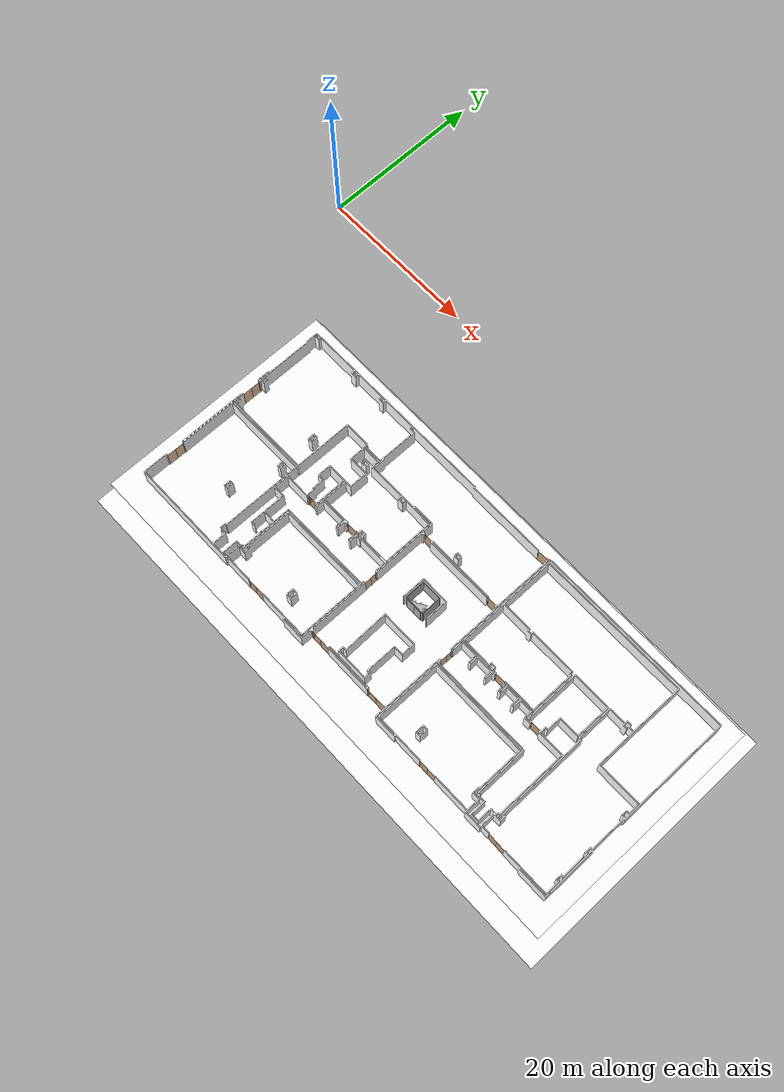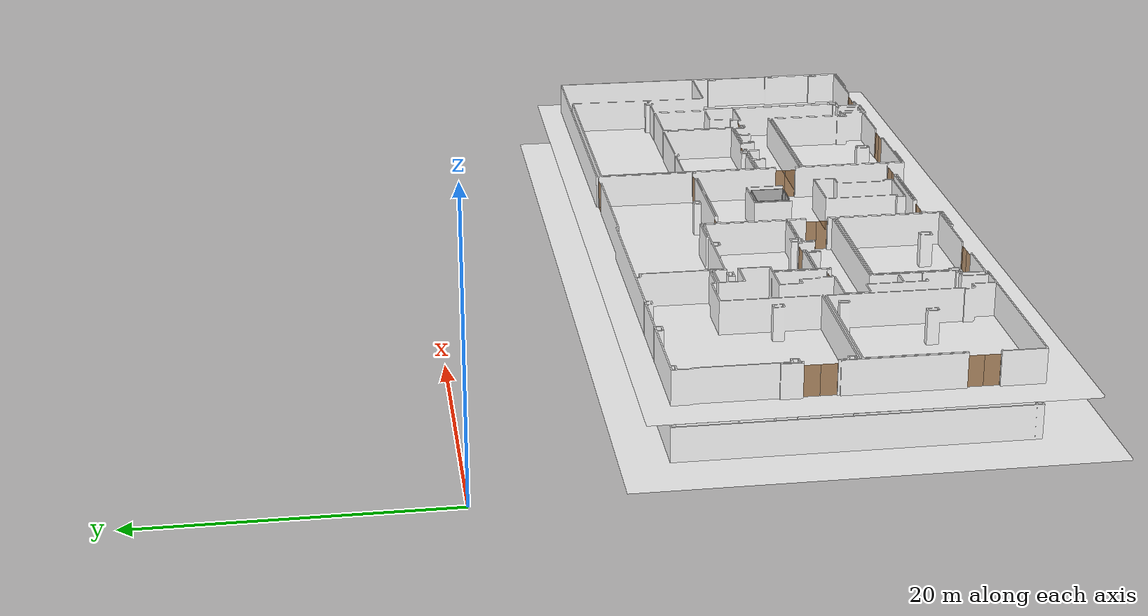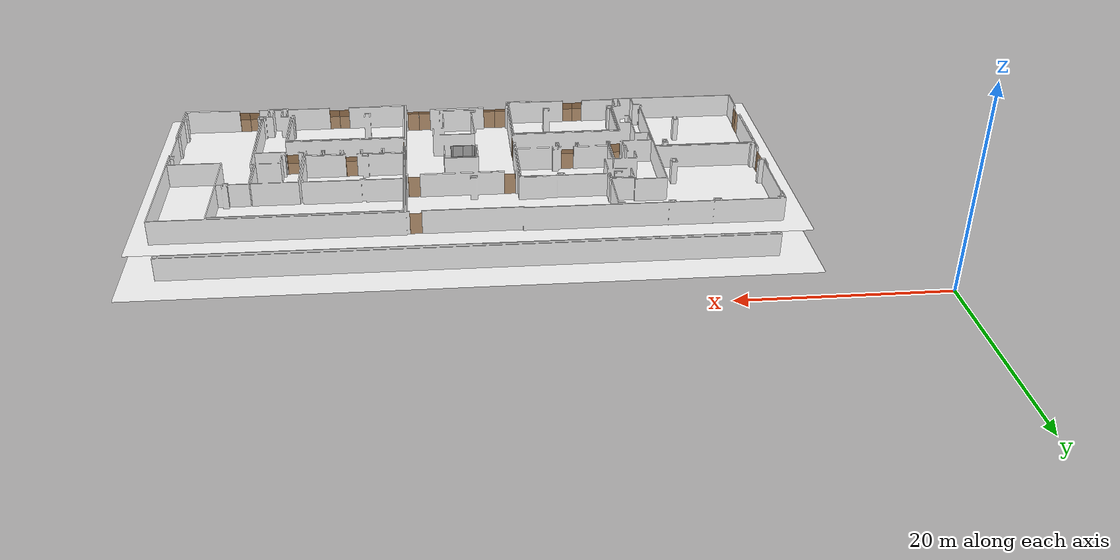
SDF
<sdf version="1.7">
 <world name="sim_world">
  <physics name="10ms" type="ode">
   <max_step_size>0.01</max_step_size>
   <real_time_factor>1.0</real_time_factor>
  </physics>
  <plugin filename="gz-sim-physics-system" name="gz::sim::systems::Physics"/>
  <plugin filename="gz-sim-user-commands-system" name="gz::sim::systems::UserCommands"/>
  <plugin filename="gz-sim-scene-broadcaster-system" name="gz::sim::systems::SceneBroadcaster"/>
  <plugin filename="libdoor.so" name="door"/>
  <plugin filename="liblift.so" name="lift"/>
  <scene><ambient>1 1 1</ambient><background>0.8 0.8 0.8</background><grid>false</grid></scene>
  <light type="directional" name="sun">
   <pose>0 0 10 0 0 0</pose>
   <diffuse>1 1 1 1</diffuse>
   <specular>0.2 0.2 0.2 1</specular>
   <attenuation>
    <range>1000</range>
    <constant>0.09</constant>
    <linear>0.001</linear>
    <quadratic>0.001</quadratic>
   </attenuation>
   <direction>-0.5 0.1 -0.9</direction>
  </light>
  <model name="puerta1">
   <pose>11.962999429963212 -23.477530657144076 0.0 0 0 1.565005116263231</pose>
   <link name="right">
    <pose>0.5918117585810255 0 1.11 0 0 0</pose>
    <visual name="right_visual">
     <geometry><box><size>1.173623517162051 0.03 2.2</size></box></geometry>
     <material>
      <ambient>0.5 0.25 0 0.6</ambient>
      <diffuse>0.5 0.25 0 0.6</diffuse>
      <pbr><metal><metalness>0.0</metalness></metal></pbr>
     </material>
    </visual>
    <collision name="right_collision">
     <geometry><box><size>1.173623517162051 0.03 2.2</size></box></geometry>
     <surface><contact><collide_bitmask>0x02</collide_bitmask></contact></surface>
    </collision>
    <inertial>
     <mass>50.0</mass>
     <inertia><ixx>20.17041666666667</ixx><iyy>25.905800666815935</iyy><izz>5.742884000149264</izz></inertia>
    </inertial>
   </link>
   <joint name="right_joint" type="revolute">
    <parent>world</parent>
    <child>right</child>
    <axis><xyz>0 0 1</xyz><limit><lower>0</lower><upper>1.57</upper></limit></axis>
    <pose>0.5918117585810255 0 0 0 0 0</pose>
   </joint>
   <link name="left">
    <pose>-0.5918117585810255 0 1.11 0 0 0</pose>
    <visual name="left_visual">
     <geometry><box><size>1.173623517162051 0.03 2.2</size></box></geometry>
     <material>
      <ambient>0.5 0.25 0 0.6</ambient>
      <diffuse>0.5 0.25 0 0.6</diffuse>
      <pbr><metal><metalness>0.0</metalness></metal></pbr>
     </material>
    </visual>
    <collision name="left_collision">
     <geometry><box><size>1.173623517162051 0.03 2.2</size></box></geometry>
     <surface><contact><collide_bitmask>0x02</collide_bitmask></contact></surface>
    </collision>
    <inertial>
     <mass>50.0</mass>
     <inertia><ixx>20.17041666666667</ixx><iyy>25.905800666815935</iyy><izz>5.742884000149264</izz></inertia>
    </inertial>
   </link>
   <joint name="left_joint" type="revolute">
    <parent>world</parent>
    <child>left</child>
    <axis><xyz>0 0 1</xyz><limit><lower>-1.57</lower><upper>0</upper></limit></axis>
    <pose>-0.5918117585810255 0 0 0 0 0</pose>
   </joint>
   <plugin name="register_component" filename="libregister_component.so">
    <component name="Door">
     <v_max_door>0.5</v_max_door>
     <a_max_door>0.3</a_max_door>
     <a_nom_door>0.15</a_nom_door>
     <dx_min_door>0.01</dx_min_door>
     <f_max_door>500.0</f_max_door>
     <ros_interface>true</ros_interface>
     <door name="puerta1" type="DoubleSwingDoor" left_joint_name="left_joint" right_joint_name="right_joint"/>
    </component>
   </plugin>
  </model>
  <model name="puerta7">
   <pose>11.955897525286552 -34.2723433223252 0.0 0 0 -1.5739164575395352</pose>
   <link name="right">
    <pose>0.5718709967881908 0 1.11 0 0 0</pose>
    <visual name="right_visual">
     <geometry><box><size>1.1337419935763815 0.03 2.2</size></box></geometry>
     <material>
      <ambient>0.5 0.25 0 0.6</ambient>
      <diffuse>0.5 0.25 0 0.6</diffuse>
      <pbr><metal><metalness>0.0</metalness></metal></pbr>
     </material>
    </visual>
    <collision name="right_collision">
     <geometry><box><size>1.1337419935763815 0.03 2.2</size></box></geometry>
     <surface><contact><collide_bitmask>0x02</collide_bitmask></contact></surface>
    </collision>
    <inertial>
     <mass>50.0</mass>
     <inertia><ixx>20.17041666666667</ixx><iyy>25.522378783327287</iyy><izz>5.359462116660616</izz></inertia>
    </inertial>
   </link>
   <joint name="right_joint" type="revolute">
    <parent>world</parent>
    <child>right</child>
    <axis><xyz>0 0 -1</xyz><limit><lower>0</lower><upper>1.57</upper></limit></axis>
    <pose>0.5718709967881908 0 0 0 0 0</pose>
   </joint>
   <link name="left">
    <pose>-0.5718709967881908 0 1.11 0 0 0</pose>
    <visual name="left_visual">
     <geometry><box><size>1.1337419935763815 0.03 2.2</size></box></geometry>
     <material>
      <ambient>0.5 0.25 0 0.6</ambient>
      <diffuse>0.5 0.25 0 0.6</diffuse>
      <pbr><metal><metalness>0.0</metalness></metal></pbr>
     </material>
    </visual>
    <collision name="left_collision">
     <geometry><box><size>1.1337419935763815 0.03 2.2</size></box></geometry>
     <surface><contact><collide_bitmask>0x02</collide_bitmask></contact></surface>
    </collision>
    <inertial>
     <mass>50.0</mass>
     <inertia><ixx>20.17041666666667</ixx><iyy>25.522378783327287</iyy><izz>5.359462116660616</izz></inertia>
    </inertial>
   </link>
   <joint name="left_joint" type="revolute">
    <parent>world</parent>
    <child>left</child>
    <axis><xyz>0 0 -1</xyz><limit><lower>-1.57</lower><upper>0</upper></limit></axis>
    <pose>-0.5718709967881908 0 0 0 0 0</pose>
   </joint>
   <plugin name="register_component" filename="libregister_component.so">
    <component name="Door">
     <v_max_door>0.5</v_max_door>
     <a_max_door>0.3</a_max_door>
     <a_nom_door>0.15</a_nom_door>
     <dx_min_door>0.01</dx_min_door>
     <f_max_door>500.0</f_max_door>
     <ros_interface>true</ros_interface>
     <door name="puerta7" type="DoubleSwingDoor" left_joint_name="left_joint" right_joint_name="right_joint"/>
    </component>
   </plugin>
  </model>
  <model name="puerta6">
   <pose>29.790228815595462 -38.21295820829428 0.0 0 0 0.010102703109197853</pose>
   <link name="right">
    <pose>0.5549249820248885 0 1.11 0 0 0</pose>
    <visual name="right_visual">
     <geometry><box><size>1.099849964049777 0.03 2.2</size></box></geometry>
     <material>
      <ambient>0.5 0.25 0 0.6</ambient>
      <diffuse>0.5 0.25 0 0.6</diffuse>
      <pbr><metal><metalness>0.0</metalness></metal></pbr>
     </material>
    </visual>
    <collision name="right_collision">
     <geometry><box><size>1.099849964049777 0.03 2.2</size></box></geometry>
     <surface><contact><collide_bitmask>0x02</collide_bitmask></contact></surface>
    </collision>
    <inertial>
     <mass>50.0</mass>
     <inertia><ixx>20.17041666666667</ixx><iyy>25.206958097584568</iyy><izz>5.044041430917899</izz></inertia>
    </inertial>
   </link>
   <joint name="right_joint" type="revolute">
    <parent>world</parent>
    <child>right</child>
    <axis><xyz>0 0 -1</xyz><limit><lower>0</lower><upper>1.57</upper></limit></axis>
    <pose>0.5549249820248885 0 0 0 0 0</pose>
   </joint>
   <link name="left">
    <pose>-0.5549249820248885 0 1.11 0 0 0</pose>
    <visual name="left_visual">
     <geometry><box><size>1.099849964049777 0.03 2.2</size></box></geometry>
     <material>
      <ambient>0.5 0.25 0 0.6</ambient>
      <diffuse>0.5 0.25 0 0.6</diffuse>
      <pbr><metal><metalness>0.0</metalness></metal></pbr>
     </material>
    </visual>
    <collision name="left_collision">
     <geometry><box><size>1.099849964049777 0.03 2.2</size></box></geometry>
     <surface><contact><collide_bitmask>0x02</collide_bitmask></contact></surface>
    </collision>
    <inertial>
     <mass>50.0</mass>
     <inertia><ixx>20.17041666666667</ixx><iyy>25.206958097584568</iyy><izz>5.044041430917899</izz></inertia>
    </inertial>
   </link>
   <joint name="left_joint" type="revolute">
    <parent>world</parent>
    <child>left</child>
    <axis><xyz>0 0 -1</xyz><limit><lower>-1.57</lower><upper>0</upper></limit></axis>
    <pose>-0.5549249820248885 0 0 0 0 0</pose>
   </joint>
   <plugin name="register_component" filename="libregister_component.so">
    <component name="Door">
     <v_max_door>0.5</v_max_door>
     <a_max_door>0.3</a_max_door>
     <a_nom_door>0.15</a_nom_door>
     <dx_min_door>0.01</dx_min_door>
     <f_max_door>500.0</f_max_door>
     <ros_interface>true</ros_interface>
     <door name="puerta6" type="DoubleSwingDoor" left_joint_name="left_joint" right_joint_name="right_joint"/>
    </component>
   </plugin>
  </model>
  <model name="puertaB1">
   <pose>38.637682729769594 -37.12627257180816 0.0 0 0 3.136013505506541</pose>
   <link name="right">
    <pose>0.6280277892987371 0 1.11 0 0 0</pose>
    <visual name="right_visual">
     <geometry><box><size>1.2460555785974743 0.03 2.2</size></box></geometry>
     <material>
      <ambient>0.5 0.25 0 0.6</ambient>
      <diffuse>0.5 0.25 0 0.6</diffuse>
      <pbr><metal><metalness>0.0</metalness></metal></pbr>
     </material>
    </visual>
    <collision name="right_collision">
     <geometry><box><size>1.2460555785974743 0.03 2.2</size></box></geometry>
     <surface><contact><collide_bitmask>0x02</collide_bitmask></contact></surface>
    </collision>
    <inertial>
     <mass>50.0</mass>
     <inertia><ixx>20.17041666666667</ixx><iyy>26.636060437307865</iyy><izz>6.473143770641194</izz></inertia>
    </inertial>
   </link>
   <joint name="right_joint" type="revolute">
    <parent>world</parent>
    <child>right</child>
    <axis><xyz>0 0 -1</xyz><limit><lower>0</lower><upper>1.57</upper></limit></axis>
    <pose>0.6280277892987371 0 0 0 0 0</pose>
   </joint>
   <link name="left">
    <pose>-0.6280277892987371 0 1.11 0 0 0</pose>
    <visual name="left_visual">
     <geometry><box><size>1.2460555785974743 0.03 2.2</size></box></geometry>
     <material>
      <ambient>0.5 0.25 0 0.6</ambient>
      <diffuse>0.5 0.25 0 0.6</diffuse>
      <pbr><metal><metalness>0.0</metalness></metal></pbr>
     </material>
    </visual>
    <collision name="left_collision">
     <geometry><box><size>1.2460555785974743 0.03 2.2</size></box></geometry>
     <surface><contact><collide_bitmask>0x02</collide_bitmask></contact></surface>
    </collision>
    <inertial>
     <mass>50.0</mass>
     <inertia><ixx>20.17041666666667</ixx><iyy>26.636060437307865</iyy><izz>6.473143770641194</izz></inertia>
    </inertial>
   </link>
   <joint name="left_joint" type="revolute">
    <parent>world</parent>
    <child>left</child>
    <axis><xyz>0 0 -1</xyz><limit><lower>-1.57</lower><upper>0</upper></limit></axis>
    <pose>-0.6280277892987371 0 0 0 0 0</pose>
   </joint>
   <plugin name="register_component" filename="libregister_component.so">
    <component name="Door">
     <v_max_door>0.5</v_max_door>
     <a_max_door>0.3</a_max_door>
     <a_nom_door>0.15</a_nom_door>
     <dx_min_door>0.01</dx_min_door>
     <f_max_door>500.0</f_max_door>
     <ros_interface>true</ros_interface>
     <door name="puertaB1" type="DoubleSwingDoor" left_joint_name="left_joint" right_joint_name="right_joint"/>
    </component>
   </plugin>
  </model>
  <model name="puertaB2">
   <pose>47.033877145293445 -37.12741500091866 0.0 0 0 -3.1370089918595623</pose>
   <link name="right">
    <pose>0.6398023558405757 0 1.11 0 0 0</pose>
    <visual name="right_visual">
     <geometry><box><size>1.2696047116811513 0.03 2.2</size></box></geometry>
     <material>
      <ambient>0.5 0.25 0 0.6</ambient>
      <diffuse>0.5 0.25 0 0.6</diffuse>
      <pbr><metal><metalness>0.0</metalness></metal></pbr>
     </material>
    </visual>
    <collision name="right_collision">
     <geometry><box><size>1.2696047116811513 0.03 2.2</size></box></geometry>
     <surface><contact><collide_bitmask>0x02</collide_bitmask></contact></surface>
    </collision>
    <inertial>
     <mass>50.0</mass>
     <inertia><ixx>20.17041666666667</ixx><iyy>26.882900516345753</iyy><izz>6.71998384967908</izz></inertia>
    </inertial>
   </link>
   <joint name="right_joint" type="revolute">
    <parent>world</parent>
    <child>right</child>
    <axis><xyz>0 0 -1</xyz><limit><lower>0</lower><upper>1.57</upper></limit></axis>
    <pose>0.6398023558405757 0 0 0 0 0</pose>
   </joint>
   <link name="left">
    <pose>-0.6398023558405757 0 1.11 0 0 0</pose>
    <visual name="left_visual">
     <geometry><box><size>1.2696047116811513 0.03 2.2</size></box></geometry>
     <material>
      <ambient>0.5 0.25 0 0.6</ambient>
      <diffuse>0.5 0.25 0 0.6</diffuse>
      <pbr><metal><metalness>0.0</metalness></metal></pbr>
     </material>
    </visual>
    <collision name="left_collision">
     <geometry><box><size>1.2696047116811513 0.03 2.2</size></box></geometry>
     <surface><contact><collide_bitmask>0x02</collide_bitmask></contact></surface>
    </collision>
    <inertial>
     <mass>50.0</mass>
     <inertia><ixx>20.17041666666667</ixx><iyy>26.882900516345753</iyy><izz>6.71998384967908</izz></inertia>
    </inertial>
   </link>
   <joint name="left_joint" type="revolute">
    <parent>world</parent>
    <child>left</child>
    <axis><xyz>0 0 -1</xyz><limit><lower>-1.57</lower><upper>0</upper></limit></axis>
    <pose>-0.6398023558405757 0 0 0 0 0</pose>
   </joint>
   <plugin name="register_component" filename="libregister_component.so">
    <component name="Door">
     <v_max_door>0.5</v_max_door>
     <a_max_door>0.3</a_max_door>
     <a_nom_door>0.15</a_nom_door>
     <dx_min_door>0.01</dx_min_door>
     <f_max_door>500.0</f_max_door>
     <ros_interface>true</ros_interface>
     <door name="puertaB2" type="DoubleSwingDoor" left_joint_name="left_joint" right_joint_name="right_joint"/>
    </component>
   </plugin>
  </model>
  <model name="puerta5">
   <pose>55.85550273947435 -38.24773751925642 0.0 0 0 0.00253646287035479</pose>
   <link name="right">
    <pose>0.5595211787744906 0 1.11 0 0 0</pose>
    <visual name="right_visual">
     <geometry><box><size>1.1090423575489812 0.03 2.2</size></box></geometry>
     <material>
      <ambient>0.5 0.25 0 0.6</ambient>
      <diffuse>0.5 0.25 0 0.6</diffuse>
      <pbr><metal><metalness>0.0</metalness></metal></pbr>
     </material>
    </visual>
    <collision name="right_collision">
     <geometry><box><size>1.1090423575489812 0.03 2.2</size></box></geometry>
     <surface><contact><collide_bitmask>0x02</collide_bitmask></contact></surface>
    </collision>
    <inertial>
     <mass>50.0</mass>
     <inertia><ixx>20.17041666666667</ixx><iyy>25.291562295157515</iyy><izz>5.128645628490842</izz></inertia>
    </inertial>
   </link>
   <joint name="right_joint" type="revolute">
    <parent>world</parent>
    <child>right</child>
    <axis><xyz>0 0 -1</xyz><limit><lower>0</lower><upper>1.57</upper></limit></axis>
    <pose>0.5595211787744906 0 0 0 0 0</pose>
   </joint>
   <link name="left">
    <pose>-0.5595211787744906 0 1.11 0 0 0</pose>
    <visual name="left_visual">
     <geometry><box><size>1.1090423575489812 0.03 2.2</size></box></geometry>
     <material>
      <ambient>0.5 0.25 0 0.6</ambient>
      <diffuse>0.5 0.25 0 0.6</diffuse>
      <pbr><metal><metalness>0.0</metalness></metal></pbr>
     </material>
    </visual>
    <collision name="left_collision">
     <geometry><box><size>1.1090423575489812 0.03 2.2</size></box></geometry>
     <surface><contact><collide_bitmask>0x02</collide_bitmask></contact></surface>
    </collision>
    <inertial>
     <mass>50.0</mass>
     <inertia><ixx>20.17041666666667</ixx><iyy>25.291562295157515</iyy><izz>5.128645628490842</izz></inertia>
    </inertial>
   </link>
   <joint name="left_joint" type="revolute">
    <parent>world</parent>
    <child>left</child>
    <axis><xyz>0 0 -1</xyz><limit><lower>-1.57</lower><upper>0</upper></limit></axis>
    <pose>-0.5595211787744906 0 0 0 0 0</pose>
   </joint>
   <plugin name="register_component" filename="libregister_component.so">
    <component name="Door">
     <v_max_door>0.5</v_max_door>
     <a_max_door>0.3</a_max_door>
     <a_nom_door>0.15</a_nom_door>
     <dx_min_door>0.01</dx_min_door>
     <f_max_door>500.0</f_max_door>
     <ros_interface>true</ros_interface>
     <door name="puerta5" type="DoubleSwingDoor" left_joint_name="left_joint" right_joint_name="right_joint"/>
    </component>
   </plugin>
  </model>
  <model name="puerta4">
   <pose>65.71122689819899 -38.2626244305521 0.0 0 0 -0.024666939195955244</pose>
   <link name="right">
    <pose>0.565615589511446 0 1.11 0 0 0</pose>
    <visual name="right_visual">
     <geometry><box><size>1.121231179022892 0.03 2.2</size></box></geometry>
     <material>
      <ambient>0.5 0.25 0 0.6</ambient>
      <diffuse>0.5 0.25 0 0.6</diffuse>
      <pbr><metal><metalness>0.0</metalness></metal></pbr>
     </material>
    </visual>
    <collision name="right_collision">
     <geometry><box><size>1.121231179022892 0.03 2.2</size></box></geometry>
     <surface><contact><collide_bitmask>0x02</collide_bitmask></contact></surface>
    </collision>
    <inertial>
     <mass>50.0</mass>
     <inertia><ixx>20.17041666666667</ixx><iyy>25.404830653387773</iyy><izz>5.2419139867211015</izz></inertia>
    </inertial>
   </link>
   <joint name="right_joint" type="revolute">
    <parent>world</parent>
    <child>right</child>
    <axis><xyz>0 0 -1</xyz><limit><lower>0</lower><upper>1.57</upper></limit></axis>
    <pose>0.565615589511446 0 0 0 0 0</pose>
   </joint>
   <link name="left">
    <pose>-0.565615589511446 0 1.11 0 0 0</pose>
    <visual name="left_visual">
     <geometry><box><size>1.121231179022892 0.03 2.2</size></box></geometry>
     <material>
      <ambient>0.5 0.25 0 0.6</ambient>
      <diffuse>0.5 0.25 0 0.6</diffuse>
      <pbr><metal><metalness>0.0</metalness></metal></pbr>
     </material>
    </visual>
    <collision name="left_collision">
     <geometry><box><size>1.121231179022892 0.03 2.2</size></box></geometry>
     <surface><contact><collide_bitmask>0x02</collide_bitmask></contact></surface>
    </collision>
    <inertial>
     <mass>50.0</mass>
     <inertia><ixx>20.17041666666667</ixx><iyy>25.404830653387773</iyy><izz>5.2419139867211015</izz></inertia>
    </inertial>
   </link>
   <joint name="left_joint" type="revolute">
    <parent>world</parent>
    <child>left</child>
    <axis><xyz>0 0 -1</xyz><limit><lower>-1.57</lower><upper>0</upper></limit></axis>
    <pose>-0.565615589511446 0 0 0 0 0</pose>
   </joint>
   <plugin name="register_component" filename="libregister_component.so">
    <component name="Door">
     <v_max_door>0.5</v_max_door>
     <a_max_door>0.3</a_max_door>
     <a_nom_door>0.15</a_nom_door>
     <dx_min_door>0.01</dx_min_door>
     <f_max_door>500.0</f_max_door>
     <ros_interface>true</ros_interface>
     <door name="puerta4" type="DoubleSwingDoor" left_joint_name="left_joint" right_joint_name="right_joint"/>
    </component>
   </plugin>
  </model>
  <model name="puertaEC">
   <pose>60.15206084789442 -27.380492492945216 0.0 0 0 -0.021615490977527397</pose>
   <link name="right">
    <pose>0 0 1.11 0 0 0</pose>
    <visual name="right_visual">
     <geometry><box><size>1.2803512290869254 0.03 2.2</size></box></geometry>
     <material>
      <ambient>0.5 0.25 0 0.6</ambient>
      <diffuse>0.5 0.25 0 0.6</diffuse>
      <pbr><metal><metalness>0.0</metalness></metal></pbr>
     </material>
    </visual>
    <collision name="right_collision">
     <geometry><box><size>1.2803512290869254 0.03 2.2</size></box></geometry>
     <surface><contact><collide_bitmask>0x02</collide_bitmask></contact></surface>
    </collision>
    <inertial>
     <mass>50.0</mass>
     <inertia><ixx>20.17041666666667</ixx><iyy>26.997080290935006</iyy><izz>6.834163624268336</izz></inertia>
    </inertial>
   </link>
   <joint name="right_joint" type="revolute">
    <parent>world</parent>
    <child>right</child>
    <axis><xyz>0 0 -1</xyz><limit><lower>0</lower><upper>1.57</upper></limit></axis>
    <pose>0.6451756145434627 0 0 0 0 0</pose>
   </joint>
   <plugin name="register_component" filename="libregister_component.so">
    <component name="Door">
     <v_max_door>0.5</v_max_door>
     <a_max_door>0.3</a_max_door>
     <a_nom_door>0.15</a_nom_door>
     <dx_min_door>0.01</dx_min_door>
     <f_max_door>500.0</f_max_door>
     <ros_interface>true</ros_interface>
     <door name="puertaEC" type="SwingDoor" left_joint_name="empty_joint" right_joint_name="right_joint"/>
    </component>
   </plugin>
  </model>
  <model name="puertaB3">
   <pose>48.694874851013125 -28.84258975723971 0.0 0 0 1.5494775355953916</pose>
   <link name="right">
    <pose>0.41934321853720863 0 1.11 0 0 0</pose>
    <visual name="right_visual">
     <geometry><box><size>0.8286864370744172 0.03 2.2</size></box></geometry>
     <material>
      <ambient>0.5 0.25 0 0.6</ambient>
      <diffuse>0.5 0.25 0 0.6</diffuse>
      <pbr><metal><metalness>0.0</metalness></metal></pbr>
     </material>
    </visual>
    <collision name="right_collision">
     <geometry><box><size>0.8286864370744172 0.03 2.2</size></box></geometry>
     <surface><contact><collide_bitmask>0x02</collide_bitmask></contact></surface>
    </collision>
    <inertial>
     <mass>50.0</mass>
     <inertia><ixx>20.17041666666667</ixx><iyy>23.028005045796224</iyy><izz>2.8650883791295505</izz></inertia>
    </inertial>
   </link>
   <joint name="right_joint" type="revolute">
    <parent>world</parent>
    <child>right</child>
    <axis><xyz>0 0 -1</xyz><limit><lower>0</lower><upper>1.57</upper></limit></axis>
    <pose>0.41934321853720863 0 0 0 0 0</pose>
   </joint>
   <link name="left">
    <pose>-0.41934321853720863 0 1.11 0 0 0</pose>
    <visual name="left_visual">
     <geometry><box><size>0.8286864370744172 0.03 2.2</size></box></geometry>
     <material>
      <ambient>0.5 0.25 0 0.6</ambient>
      <diffuse>0.5 0.25 0 0.6</diffuse>
      <pbr><metal><metalness>0.0</metalness></metal></pbr>
     </material>
    </visual>
    <collision name="left_collision">
     <geometry><box><size>0.8286864370744172 0.03 2.2</size></box></geometry>
     <surface><contact><collide_bitmask>0x02</collide_bitmask></contact></surface>
    </collision>
    <inertial>
     <mass>50.0</mass>
     <inertia><ixx>20.17041666666667</ixx><iyy>23.028005045796224</iyy><izz>2.8650883791295505</izz></inertia>
    </inertial>
   </link>
   <joint name="left_joint" type="revolute">
    <parent>world</parent>
    <child>left</child>
    <axis><xyz>0 0 -1</xyz><limit><lower>-1.57</lower><upper>0</upper></limit></axis>
    <pose>-0.41934321853720863 0 0 0 0 0</pose>
   </joint>
   <plugin name="register_component" filename="libregister_component.so">
    <component name="Door">
     <v_max_door>0.5</v_max_door>
     <a_max_door>0.3</a_max_door>
     <a_nom_door>0.15</a_nom_door>
     <dx_min_door>0.01</dx_min_door>
     <f_max_door>500.0</f_max_door>
     <ros_interface>true</ros_interface>
     <door name="puertaB3" type="DoubleSwingDoor" left_joint_name="left_joint" right_joint_name="right_joint"/>
    </component>
   </plugin>
  </model>
  <model name="puertaB4">
   <pose>37.19075503964348 -28.809400424936527 0.0 0 0 -1.560095286636433</pose>
   <link name="right">
    <pose>0.432546071391894 0 1.11 0 0 0</pose>
    <visual name="right_visual">
     <geometry><box><size>0.855092142783788 0.03 2.2</size></box></geometry>
     <material>
      <ambient>0.5 0.25 0 0.6</ambient>
      <diffuse>0.5 0.25 0 0.6</diffuse>
      <pbr><metal><metalness>0.0</metalness></metal></pbr>
     </material>
    </visual>
    <collision name="right_collision">
     <geometry><box><size>0.855092142783788 0.03 2.2</size></box></geometry>
     <surface><contact><collide_bitmask>0x02</collide_bitmask></contact></surface>
    </collision>
    <inertial>
     <mass>50.0</mass>
     <inertia><ixx>20.17041666666667</ixx><iyy>23.21326071937738</iyy><izz>3.050344052710709</izz></inertia>
    </inertial>
   </link>
   <joint name="right_joint" type="revolute">
    <parent>world</parent>
    <child>right</child>
    <axis><xyz>0 0 -1</xyz><limit><lower>0</lower><upper>1.57</upper></limit></axis>
    <pose>0.432546071391894 0 0 0 0 0</pose>
   </joint>
   <link name="left">
    <pose>-0.432546071391894 0 1.11 0 0 0</pose>
    <visual name="left_visual">
     <geometry><box><size>0.855092142783788 0.03 2.2</size></box></geometry>
     <material>
      <ambient>0.5 0.25 0 0.6</ambient>
      <diffuse>0.5 0.25 0 0.6</diffuse>
      <pbr><metal><metalness>0.0</metalness></metal></pbr>
     </material>
    </visual>
    <collision name="left_collision">
     <geometry><box><size>0.855092142783788 0.03 2.2</size></box></geometry>
     <surface><contact><collide_bitmask>0x02</collide_bitmask></contact></surface>
    </collision>
    <inertial>
     <mass>50.0</mass>
     <inertia><ixx>20.17041666666667</ixx><iyy>23.21326071937738</iyy><izz>3.050344052710709</izz></inertia>
    </inertial>
   </link>
   <joint name="left_joint" type="revolute">
    <parent>world</parent>
    <child>left</child>
    <axis><xyz>0 0 -1</xyz><limit><lower>-1.57</lower><upper>0</upper></limit></axis>
    <pose>-0.432546071391894 0 0 0 0 0</pose>
   </joint>
   <plugin name="register_component" filename="libregister_component.so">
    <component name="Door">
     <v_max_door>0.5</v_max_door>
     <a_max_door>0.3</a_max_door>
     <a_nom_door>0.15</a_nom_door>
     <dx_min_door>0.01</dx_min_door>
     <f_max_door>500.0</f_max_door>
     <ros_interface>true</ros_interface>
     <door name="puertaB4" type="DoubleSwingDoor" left_joint_name="left_joint" right_joint_name="right_joint"/>
    </component>
   </plugin>
  </model>
  <model name="puertaEA">
   <pose>26.458987972694775 -27.398771358713326 0.0 0 0 0.06506101426287529</pose>
   <link name="right">
    <pose>0 0 1.11 0 0 0</pose>
    <visual name="right_visual">
     <geometry><box><size>1.1211130812435688 0.03 2.2</size></box></geometry>
     <material>
      <ambient>0.5 0.25 0 0.6</ambient>
      <diffuse>0.5 0.25 0 0.6</diffuse>
      <pbr><metal><metalness>0.0</metalness></metal></pbr>
     </material>
    </visual>
    <collision name="right_collision">
     <geometry><box><size>1.1211130812435688 0.03 2.2</size></box></geometry>
     <surface><contact><collide_bitmask>0x02</collide_bitmask></contact></surface>
    </collision>
    <inertial>
     <mass>50.0</mass>
     <inertia><ixx>20.17041666666667</ixx><iyy>25.40372725389771</iyy><izz>5.240810587231037</izz></inertia>
    </inertial>
   </link>
   <joint name="right_joint" type="revolute">
    <parent>world</parent>
    <child>right</child>
    <axis><xyz>0 0 -1</xyz><limit><lower>0</lower><upper>1.57</upper></limit></axis>
    <pose>0.5655565406217844 0 0 0 0 0</pose>
   </joint>
   <plugin name="register_component" filename="libregister_component.so">
    <component name="Door">
     <v_max_door>0.5</v_max_door>
     <a_max_door>0.3</a_max_door>
     <a_nom_door>0.15</a_nom_door>
     <dx_min_door>0.01</dx_min_door>
     <f_max_door>500.0</f_max_door>
     <ros_interface>true</ros_interface>
     <door name="puertaEA" type="SwingDoor" left_joint_name="empty_joint" right_joint_name="right_joint"/>
    </component>
   </plugin>
  </model>
  <model name="puerta2">
   <pose>31.62593573188485 -26.463345691982276 0.0 0 0 0.010278512859814274</pose>
   <link name="right">
    <pose>0 0 1.11 0 0 0</pose>
    <visual name="right_visual">
     <geometry><box><size>1.355875595919269 0.03 2.2</size></box></geometry>
     <material>
      <ambient>0.5 0.25 0 0.6</ambient>
      <diffuse>0.5 0.25 0 0.6</diffuse>
      <pbr><metal><metalness>0.0</metalness></metal></pbr>
     </material>
    </visual>
    <collision name="right_collision">
     <geometry><box><size>1.355875595919269 0.03 2.2</size></box></geometry>
     <surface><contact><collide_bitmask>0x02</collide_bitmask></contact></surface>
    </collision>
    <inertial>
     <mass>50.0</mass>
     <inertia><ixx>20.17041666666667</ixx><iyy>27.82666096503931</iyy><izz>7.663744298372636</izz></inertia>
    </inertial>
   </link>
   <joint name="right_joint" type="revolute">
    <parent>world</parent>
    <child>right</child>
    <axis><xyz>0 0 -1</xyz><limit><lower>0</lower><upper>1.57</upper></limit></axis>
    <pose>0.6829377979596345 0 0 0 0 0</pose>
   </joint>
   <plugin name="register_component" filename="libregister_component.so">
    <component name="Door">
     <v_max_door>0.5</v_max_door>
     <a_max_door>0.3</a_max_door>
     <a_nom_door>0.15</a_nom_door>
     <dx_min_door>0.01</dx_min_door>
     <f_max_door>500.0</f_max_door>
     <ros_interface>true</ros_interface>
     <door name="puerta2" type="SwingDoor" left_joint_name="empty_joint" right_joint_name="right_joint"/>
    </component>
   </plugin>
  </model>
  <model name="w">
   <pose>47.53542708004542 -13.956538227798013 0.0 0 0 -3.132897220578016</pose>
   <link name="right">
    <pose>0 0 1.11 0 0 0</pose>
    <visual name="right_visual">
     <geometry><box><size>1.2334103184774419 0.03 2.2</size></box></geometry>
     <material>
      <ambient>0.5 0.25 0 0.6</ambient>
      <diffuse>0.5 0.25 0 0.6</diffuse>
      <pbr><metal><metalness>0.0</metalness></metal></pbr>
     </material>
    </visual>
    <collision name="right_collision">
     <geometry><box><size>1.2334103184774419 0.03 2.2</size></box></geometry>
     <surface><contact><collide_bitmask>0x02</collide_bitmask></contact></surface>
    </collision>
    <inertial>
     <mass>50.0</mass>
     <inertia><ixx>20.17041666666667</ixx><iyy>26.505420890527606</iyy><izz>6.342504223860936</izz></inertia>
    </inertial>
   </link>
   <joint name="right_joint" type="revolute">
    <parent>world</parent>
    <child>right</child>
    <axis><xyz>0 0 1</xyz><limit><lower>0</lower><upper>1.57</upper></limit></axis>
    <pose>0.6217051592387209 0 0 0 0 0</pose>
   </joint>
   <plugin name="register_component" filename="libregister_component.so">
    <component name="Door">
     <v_max_door>0.5</v_max_door>
     <a_max_door>0.3</a_max_door>
     <a_nom_door>0.15</a_nom_door>
     <dx_min_door>0.01</dx_min_door>
     <f_max_door>500.0</f_max_door>
     <ros_interface>true</ros_interface>
     <door name="w" type="SwingDoor" left_joint_name="empty_joint" right_joint_name="right_joint"/>
    </component>
   </plugin>
  </model>
  <model name="puertaB6">
   <pose>47.64739691049482 -21.400888974734656 0.0 0 0 -0.005553022187559174</pose>
   <link name="right">
    <pose>0 0 1.11 0 0 0</pose>
    <visual name="right_visual">
     <geometry><box><size>1.2583278648812628 0.03 2.2</size></box></geometry>
     <material>
      <ambient>0.5 0.25 0 0.6</ambient>
      <diffuse>0.5 0.25 0 0.6</diffuse>
      <pbr><metal><metalness>0.0</metalness></metal></pbr>
     </material>
    </visual>
    <collision name="right_collision">
     <geometry><box><size>1.2583278648812628 0.03 2.2</size></box></geometry>
     <surface><contact><collide_bitmask>0x02</collide_bitmask></contact></surface>
    </collision>
    <inertial>
     <mass>50.0</mass>
     <inertia><ixx>20.17041666666667</ixx><iyy>26.764120898069326</iyy><izz>6.601204231402656</izz></inertia>
    </inertial>
   </link>
   <joint name="right_joint" type="revolute">
    <parent>world</parent>
    <child>right</child>
    <axis><xyz>0 0 -1</xyz><limit><lower>0</lower><upper>1.57</upper></limit></axis>
    <pose>0.6341639324406314 0 0 0 0 0</pose>
   </joint>
   <plugin name="register_component" filename="libregister_component.so">
    <component name="Door">
     <v_max_door>0.5</v_max_door>
     <a_max_door>0.3</a_max_door>
     <a_nom_door>0.15</a_nom_door>
     <dx_min_door>0.01</dx_min_door>
     <f_max_door>500.0</f_max_door>
     <ros_interface>true</ros_interface>
     <door name="puertaB6" type="SwingDoor" left_joint_name="empty_joint" right_joint_name="right_joint"/>
    </component>
   </plugin>
  </model>
  <model name="puertaB5">
   <pose>38.01422265354484 -21.382527665628672 0.0 0 0 3.117840569362342</pose>
   <link name="right">
    <pose>0 0 1.11 0 0 0</pose>
    <visual name="right_visual">
     <geometry><box><size>1.2396752796384625 0.03 2.2</size></box></geometry>
     <material>
      <ambient>0.5 0.25 0 0.6</ambient>
      <diffuse>0.5 0.25 0 0.6</diffuse>
      <pbr><metal><metalness>0.0</metalness></metal></pbr>
     </material>
    </visual>
    <collision name="right_collision">
     <geometry><box><size>1.2396752796384625 0.03 2.2</size></box></geometry>
     <surface><contact><collide_bitmask>0x02</collide_bitmask></contact></surface>
    </collision>
    <inertial>
     <mass>50.0</mass>
     <inertia><ixx>20.17041666666667</ixx><iyy>26.56997832894459</iyy><izz>6.4070616622779175</izz></inertia>
    </inertial>
   </link>
   <joint name="right_joint" type="revolute">
    <parent>world</parent>
    <child>right</child>
    <axis><xyz>0 0 1</xyz><limit><lower>0</lower><upper>1.57</upper></limit></axis>
    <pose>0.6248376398192312 0 0 0 0 0</pose>
   </joint>
   <plugin name="register_component" filename="libregister_component.so">
    <component name="Door">
     <v_max_door>0.5</v_max_door>
     <a_max_door>0.3</a_max_door>
     <a_nom_door>0.15</a_nom_door>
     <dx_min_door>0.01</dx_min_door>
     <f_max_door>500.0</f_max_door>
     <ros_interface>true</ros_interface>
     <door name="puertaB5" type="SwingDoor" left_joint_name="empty_joint" right_joint_name="right_joint"/>
    </component>
   </plugin>
  </model>
  <model name="puerta3">
   <pose>54.07758860303299 -26.469493609463562 0.0 0 0 0.03399783386577453</pose>
   <link name="right">
    <pose>0 0 1.11 0 0 0</pose>
    <visual name="right_visual">
     <geometry><box><size>1.2526073532450872 0.03 2.2</size></box></geometry>
     <material>
      <ambient>0.5 0.25 0 0.6</ambient>
      <diffuse>0.5 0.25 0 0.6</diffuse>
      <pbr><metal><metalness>0.0</metalness></metal></pbr>
     </material>
    </visual>
    <collision name="right_collision">
     <geometry><box><size>1.2526073532450872 0.03 2.2</size></box></geometry>
     <surface><contact><collide_bitmask>0x02</collide_bitmask></contact></surface>
    </collision>
    <inertial>
     <mass>50.0</mass>
     <inertia><ixx>20.17041666666667</ixx><iyy>26.704271589181932</iyy><izz>6.541354922515261</izz></inertia>
    </inertial>
   </link>
   <joint name="right_joint" type="revolute">
    <parent>world</parent>
    <child>right</child>
    <axis><xyz>0 0 1</xyz><limit><lower>0</lower><upper>1.57</upper></limit></axis>
    <pose>0.6313036766225436 0 0 0 0 0</pose>
   </joint>
   <plugin name="register_component" filename="libregister_component.so">
    <component name="Door">
     <v_max_door>0.5</v_max_door>
     <a_max_door>0.3</a_max_door>
     <a_nom_door>0.15</a_nom_door>
     <dx_min_door>0.01</dx_min_door>
     <f_max_door>500.0</f_max_door>
     <ros_interface>true</ros_interface>
     <door name="puerta3" type="SwingDoor" left_joint_name="empty_joint" right_joint_name="right_joint"/>
    </component>
   </plugin>
  </model>
  <include><name>industrial_baixa</name><uri>model://industrial_baixa</uri></include>
  <model name="prueta-s1">
   <pose>14.015022137387977 -17.470787204386287 -4.0 0 0 -1.607727183249277</pose>
   <link name="right">
    <pose>0 0 1.11 0 0 0</pose>
    <visual name="right_visual">
     <geometry><box><size>1.050546027334926 0.03 2.2</size></box></geometry>
     <material>
      <ambient>0.5 0.25 0 0.6</ambient>
      <diffuse>0.5 0.25 0 0.6</diffuse>
      <pbr><metal><metalness>0.0</metalness></metal></pbr>
     </material>
    </visual>
    <collision name="right_collision">
     <geometry><box><size>1.050546027334926 0.03 2.2</size></box></geometry>
     <surface><contact><collide_bitmask>0x02</collide_bitmask></contact></surface>
    </collision>
    <inertial>
     <mass>50.0</mass>
     <inertia><ixx>20.17041666666667</ixx><iyy>24.765195648121654</iyy><izz>4.60227898145498</izz></inertia>
    </inertial>
   </link>
   <joint name="right_joint" type="revolute">
    <parent>world</parent>
    <child>right</child>
    <axis><xyz>0 0 1</xyz><limit><lower>0</lower><upper>1.57</upper></limit></axis>
    <pose>0.530273013667463 0 0 0 0 0</pose>
   </joint>
   <plugin name="register_component" filename="libregister_component.so">
    <component name="Door">
     <v_max_door>0.5</v_max_door>
     <a_max_door>0.3</a_max_door>
     <a_nom_door>0.15</a_nom_door>
     <dx_min_door>0.01</dx_min_door>
     <f_max_door>500.0</f_max_door>
     <ros_interface>true</ros_interface>
     <door name="prueta-s1" type="SwingDoor" left_joint_name="empty_joint" right_joint_name="right_joint"/>
    </component>
   </plugin>
  </model>
  <model name="prueta-s2">
   <pose>14.843828464332827 -18.361168940498054 -4.0 0 0 0.05935155146143872</pose>
   <link name="right">
    <pose>0 0 1.11 0 0 0</pose>
    <visual name="right_visual">
     <geometry><box><size>1.113312072848375 0.03 2.2</size></box></geometry>
     <material>
      <ambient>0.5 0.25 0 0.6</ambient>
      <diffuse>0.5 0.25 0 0.6</diffuse>
      <pbr><metal><metalness>0.0</metalness></metal></pbr>
     </material>
    </visual>
    <collision name="right_collision">
     <geometry><box><size>1.113312072848375 0.03 2.2</size></box></geometry>
     <surface><contact><collide_bitmask>0x02</collide_bitmask></contact></surface>
    </collision>
    <inertial>
     <mass>50.0</mass>
     <inertia><ixx>20.17041666666667</ixx><iyy>25.331099048124777</iyy><izz>5.168182381458106</izz></inertia>
    </inertial>
   </link>
   <joint name="right_joint" type="revolute">
    <parent>world</parent>
    <child>right</child>
    <axis><xyz>0 0 1</xyz><limit><lower>0</lower><upper>1.57</upper></limit></axis>
    <pose>0.5616560364241875 0 0 0 0 0</pose>
   </joint>
   <plugin name="register_component" filename="libregister_component.so">
    <component name="Door">
     <v_max_door>0.5</v_max_door>
     <a_max_door>0.3</a_max_door>
     <a_nom_door>0.15</a_nom_door>
     <dx_min_door>0.01</dx_min_door>
     <f_max_door>500.0</f_max_door>
     <ros_interface>true</ros_interface>
     <door name="prueta-s2" type="SwingDoor" left_joint_name="empty_joint" right_joint_name="right_joint"/>
    </component>
   </plugin>
  </model>
  <model name="prueta-s4">
   <pose>17.505466105682967 -18.19578503164263 -4.0 0 0 0.039095871462473154</pose>
   <link name="right">
    <pose>0 0 1.11 0 0 0</pose>
    <visual name="right_visual">
     <geometry><box><size>1.0456715581942553 0.03 2.2</size></box></geometry>
     <material>
      <ambient>0.5 0.25 0 0.6</ambient>
      <diffuse>0.5 0.25 0 0.6</diffuse>
      <pbr><metal><metalness>0.0</metalness></metal></pbr>
     </material>
    </visual>
    <collision name="right_collision">
     <geometry><box><size>1.0456715581942553 0.03 2.2</size></box></geometry>
     <surface><contact><collide_bitmask>0x02</collide_bitmask></contact></surface>
    </collision>
    <inertial>
     <mass>50.0</mass>
     <inertia><ixx>20.17041666666667</ixx><iyy>24.722620865068343</iyy><izz>4.559704198401674</izz></inertia>
    </inertial>
   </link>
   <joint name="right_joint" type="revolute">
    <parent>world</parent>
    <child>right</child>
    <axis><xyz>0 0 1</xyz><limit><lower>0</lower><upper>1.57</upper></limit></axis>
    <pose>0.5278357790971276 0 0 0 0 0</pose>
   </joint>
   <plugin name="register_component" filename="libregister_component.so">
    <component name="Door">
     <v_max_door>0.5</v_max_door>
     <a_max_door>0.3</a_max_door>
     <a_nom_door>0.15</a_nom_door>
     <dx_min_door>0.01</dx_min_door>
     <f_max_door>500.0</f_max_door>
     <ros_interface>true</ros_interface>
     <door name="prueta-s4" type="SwingDoor" left_joint_name="empty_joint" right_joint_name="right_joint"/>
    </component>
   </plugin>
  </model>
  <model name="prueta-s3">
   <pose>16.559952859953974 -16.792732557051146 -4.0 0 0 -0.010124649508979063</pose>
   <link name="right">
    <pose>0 0 1.11 0 0 0</pose>
    <visual name="right_visual">
     <geometry><box><size>1.1013704055704303 0.03 2.2</size></box></geometry>
     <material>
      <ambient>0.5 0.25 0 0.6</ambient>
      <diffuse>0.5 0.25 0 0.6</diffuse>
      <pbr><metal><metalness>0.0</metalness></metal></pbr>
     </material>
    </visual>
    <collision name="right_collision">
     <geometry><box><size>1.1013704055704303 0.03 2.2</size></box></geometry>
     <surface><contact><collide_bitmask>0x02</collide_bitmask></contact></surface>
    </collision>
    <inertial>
     <mass>50.0</mass>
     <inertia><ixx>20.17041666666667</ixx><iyy>25.22090320944323</iyy><izz>5.0579865427765585</izz></inertia>
    </inertial>
   </link>
   <joint name="right_joint" type="revolute">
    <parent>world</parent>
    <child>right</child>
    <axis><xyz>0 0 -1</xyz><limit><lower>0</lower><upper>1.57</upper></limit></axis>
    <pose>0.5556852027852152 0 0 0 0 0</pose>
   </joint>
   <plugin name="register_component" filename="libregister_component.so">
    <component name="Door">
     <v_max_door>0.5</v_max_door>
     <a_max_door>0.3</a_max_door>
     <a_nom_door>0.15</a_nom_door>
     <dx_min_door>0.01</dx_min_door>
     <f_max_door>500.0</f_max_door>
     <ros_interface>true</ros_interface>
     <door name="prueta-s3" type="SwingDoor" left_joint_name="empty_joint" right_joint_name="right_joint"/>
    </component>
   </plugin>
  </model>
  <model name="prueta-s5">
   <pose>19.8027270960298 -16.788332096193322 -4.0 0 0 0.016071981660298013</pose>
   <link name="right">
    <pose>0 0 1.11 0 0 0</pose>
    <visual name="right_visual">
     <geometry><box><size>1.1190847544436615 0.03 2.2</size></box></geometry>
     <material>
      <ambient>0.5 0.25 0 0.6</ambient>
      <diffuse>0.5 0.25 0 0.6</diffuse>
      <pbr><metal><metalness>0.0</metalness></metal></pbr>
     </material>
    </visual>
    <collision name="right_collision">
     <geometry><box><size>1.1190847544436615 0.03 2.2</size></box></geometry>
     <surface><contact><collide_bitmask>0x02</collide_bitmask></contact></surface>
    </collision>
    <inertial>
     <mass>50.0</mass>
     <inertia><ixx>20.17041666666667</ixx><iyy>25.384794531784298</iyy><izz>5.221877865117626</izz></inertia>
    </inertial>
   </link>
   <joint name="right_joint" type="revolute">
    <parent>world</parent>
    <child>right</child>
    <axis><xyz>0 0 -1</xyz><limit><lower>0</lower><upper>1.57</upper></limit></axis>
    <pose>0.5645423772218308 0 0 0 0 0</pose>
   </joint>
   <plugin name="register_component" filename="libregister_component.so">
    <component name="Door">
     <v_max_door>0.5</v_max_door>
     <a_max_door>0.3</a_max_door>
     <a_nom_door>0.15</a_nom_door>
     <dx_min_door>0.01</dx_min_door>
     <f_max_door>500.0</f_max_door>
     <ros_interface>true</ros_interface>
     <door name="prueta-s5" type="SwingDoor" left_joint_name="empty_joint" right_joint_name="right_joint"/>
    </component>
   </plugin>
  </model>
  <model name="prueta-s6">
   <pose>20.335089202178093 -18.383923782290463 -4.0 0 0 0.00044923060630432403</pose>
   <link name="right">
    <pose>0 0 1.11 0 0 0</pose>
    <visual name="right_visual">
     <geometry><box><size>1.1439802537445727 0.03 2.2</size></box></geometry>
     <material>
      <ambient>0.5 0.25 0 0.6</ambient>
      <diffuse>0.5 0.25 0 0.6</diffuse>
      <pbr><metal><metalness>0.0</metalness></metal></pbr>
     </material>
    </visual>
    <collision name="right_collision">
     <geometry><box><size>1.1439802537445727 0.03 2.2</size></box></geometry>
     <surface><contact><collide_bitmask>0x02</collide_bitmask></contact></surface>
    </collision>
    <inertial>
     <mass>50.0</mass>
     <inertia><ixx>20.17041666666667</ixx><iyy>25.61954508732291</iyy><izz>5.456628420656237</izz></inertia>
    </inertial>
   </link>
   <joint name="right_joint" type="revolute">
    <parent>world</parent>
    <child>right</child>
    <axis><xyz>0 0 1</xyz><limit><lower>0</lower><upper>1.57</upper></limit></axis>
    <pose>0.5769901268722863 0 0 0 0 0</pose>
   </joint>
   <plugin name="register_component" filename="libregister_component.so">
    <component name="Door">
     <v_max_door>0.5</v_max_door>
     <a_max_door>0.3</a_max_door>
     <a_nom_door>0.15</a_nom_door>
     <dx_min_door>0.01</dx_min_door>
     <f_max_door>500.0</f_max_door>
     <ros_interface>true</ros_interface>
     <door name="prueta-s6" type="SwingDoor" left_joint_name="empty_joint" right_joint_name="right_joint"/>
    </component>
   </plugin>
  </model>
  <model name="prueta-s9">
   <pose>21.932421132151227 -19.23533883307018 -4.0 0 0 3.1057464408848157</pose>
   <link name="right">
    <pose>0 0 1.11 0 0 0</pose>
    <visual name="right_visual">
     <geometry><box><size>1.3431124294630568 0.03 2.2</size></box></geometry>
     <material>
      <ambient>0.5 0.25 0 0.6</ambient>
      <diffuse>0.5 0.25 0 0.6</diffuse>
      <pbr><metal><metalness>0.0</metalness></metal></pbr>
     </material>
    </visual>
    <collision name="right_collision">
     <geometry><box><size>1.3431124294630568 0.03 2.2</size></box></geometry>
     <surface><contact><collide_bitmask>0x02</collide_bitmask></contact></surface>
    </collision>
    <inertial>
     <mass>50.0</mass>
     <inertia><ixx>20.17041666666667</ixx><iyy>27.68312915907565</iyy><izz>7.5202124924089775</izz></inertia>
    </inertial>
   </link>
   <joint name="right_joint" type="revolute">
    <parent>world</parent>
    <child>right</child>
    <axis><xyz>0 0 1</xyz><limit><lower>0</lower><upper>1.57</upper></limit></axis>
    <pose>0.6765562147315284 0 0 0 0 0</pose>
   </joint>
   <plugin name="register_component" filename="libregister_component.so">
    <component name="Door">
     <v_max_door>0.5</v_max_door>
     <a_max_door>0.3</a_max_door>
     <a_nom_door>0.15</a_nom_door>
     <dx_min_door>0.01</dx_min_door>
     <f_max_door>500.0</f_max_door>
     <ros_interface>true</ros_interface>
     <door name="prueta-s9" type="SwingDoor" left_joint_name="empty_joint" right_joint_name="right_joint"/>
    </component>
   </plugin>
  </model>
  <model name="prueta-s7">
   <pose>21.431457802256155 -16.790544127785083 -4.0 0 0 3.12053357353771</pose>
   <link name="right">
    <pose>0 0 1.11 0 0 0</pose>
    <visual name="right_visual">
     <geometry><box><size>1.0838990476852095 0.03 2.2</size></box></geometry>
     <material>
      <ambient>0.5 0.25 0 0.6</ambient>
      <diffuse>0.5 0.25 0 0.6</diffuse>
      <pbr><metal><metalness>0.0</metalness></metal></pbr>
     </material>
    </visual>
    <collision name="right_collision">
     <geometry><box><size>1.0838990476852095 0.03 2.2</size></box></geometry>
     <surface><contact><collide_bitmask>0x02</collide_bitmask></contact></surface>
    </collision>
    <inertial>
     <mass>50.0</mass>
     <inertia><ixx>20.17041666666667</ixx><iyy>25.061821439887105</iyy><izz>4.898904773220433</izz></inertia>
    </inertial>
   </link>
   <joint name="right_joint" type="revolute">
    <parent>world</parent>
    <child>right</child>
    <axis><xyz>0 0 1</xyz><limit><lower>0</lower><upper>1.57</upper></limit></axis>
    <pose>0.5469495238426048 0 0 0 0 0</pose>
   </joint>
   <plugin name="register_component" filename="libregister_component.so">
    <component name="Door">
     <v_max_door>0.5</v_max_door>
     <a_max_door>0.3</a_max_door>
     <a_nom_door>0.15</a_nom_door>
     <dx_min_door>0.01</dx_min_door>
     <f_max_door>500.0</f_max_door>
     <ros_interface>true</ros_interface>
     <door name="prueta-s7" type="SwingDoor" left_joint_name="empty_joint" right_joint_name="right_joint"/>
    </component>
   </plugin>
  </model>
  <model name="prueta-s8">
   <pose>22.87560166956552 -18.17167159183514 -4.0 0 0 -1.5754039942402178</pose>
   <link name="right">
    <pose>0 0 1.11 0 0 0</pose>
    <visual name="right_visual">
     <geometry><box><size>1.154239240255232 0.03 2.2</size></box></geometry>
     <material>
      <ambient>0.5 0.25 0 0.6</ambient>
      <diffuse>0.5 0.25 0 0.6</diffuse>
      <pbr><metal><metalness>0.0</metalness></metal></pbr>
     </material>
    </visual>
    <collision name="right_collision">
     <geometry><box><size>1.154239240255232 0.03 2.2</size></box></geometry>
     <surface><contact><collide_bitmask>0x02</collide_bitmask></contact></surface>
    </collision>
    <inertial>
     <mass>50.0</mass>
     <inertia><ixx>20.17041666666667</ixx><iyy>25.717784265604067</iyy><izz>5.5548675989373955</izz></inertia>
    </inertial>
   </link>
   <joint name="right_joint" type="revolute">
    <parent>world</parent>
    <child>right</child>
    <axis><xyz>0 0 -1</xyz><limit><lower>0</lower><upper>1.57</upper></limit></axis>
    <pose>0.582119620127616 0 0 0 0 0</pose>
   </joint>
   <plugin name="register_component" filename="libregister_component.so">
    <component name="Door">
     <v_max_door>0.5</v_max_door>
     <a_max_door>0.3</a_max_door>
     <a_nom_door>0.15</a_nom_door>
     <dx_min_door>0.01</dx_min_door>
     <f_max_door>500.0</f_max_door>
     <ros_interface>true</ros_interface>
     <door name="prueta-s8" type="SwingDoor" left_joint_name="empty_joint" right_joint_name="right_joint"/>
    </component>
   </plugin>
  </model>
  <model name="prueta-s10">
   <pose>21.92129237993227 -25.10320048827763 -4.0 0 0 3.1414374505707454</pose>
   <link name="right">
    <pose>0 0 1.11 0 0 0</pose>
    <visual name="right_visual">
     <geometry><box><size>1.3146919536133659 0.03 2.2</size></box></geometry>
     <material>
      <ambient>0.5 0.25 0 0.6</ambient>
      <diffuse>0.5 0.25 0 0.6</diffuse>
      <pbr><metal><metalness>0.0</metalness></metal></pbr>
     </material>
    </visual>
    <collision name="right_collision">
     <geometry><box><size>1.3146919536133659 0.03 2.2</size></box></geometry>
     <surface><contact><collide_bitmask>0x02</collide_bitmask></contact></surface>
    </collision>
    <inertial>
     <mass>50.0</mass>
     <inertia><ixx>20.17041666666667</ixx><iyy>27.368395553732206</iyy><izz>7.205478887065536</izz></inertia>
    </inertial>
   </link>
   <joint name="right_joint" type="revolute">
    <parent>world</parent>
    <child>right</child>
    <axis><xyz>0 0 1</xyz><limit><lower>0</lower><upper>1.57</upper></limit></axis>
    <pose>0.662345976806683 0 0 0 0 0</pose>
   </joint>
   <plugin name="register_component" filename="libregister_component.so">
    <component name="Door">
     <v_max_door>0.5</v_max_door>
     <a_max_door>0.3</a_max_door>
     <a_nom_door>0.15</a_nom_door>
     <dx_min_door>0.01</dx_min_door>
     <f_max_door>500.0</f_max_door>
     <ros_interface>true</ros_interface>
     <door name="prueta-s10" type="SwingDoor" left_joint_name="empty_joint" right_joint_name="right_joint"/>
    </component>
   </plugin>
  </model>
  <model name="prueta-s11">
   <pose>22.11906218434565 -27.566535455570595 -4.0 0 0 3.120320365945217</pose>
   <link name="right">
    <pose>0 0 1.11 0 0 0</pose>
    <visual name="right_visual">
     <geometry><box><size>1.3247090317254433 0.03 2.2</size></box></geometry>
     <material>
      <ambient>0.5 0.25 0 0.6</ambient>
      <diffuse>0.5 0.25 0 0.6</diffuse>
      <pbr><metal><metalness>0.0</metalness></metal></pbr>
     </material>
    </visual>
    <collision name="right_collision">
     <geometry><box><size>1.3247090317254433 0.03 2.2</size></box></geometry>
     <surface><contact><collide_bitmask>0x02</collide_bitmask></contact></surface>
    </collision>
    <inertial>
     <mass>50.0</mass>
     <inertia><ixx>20.17041666666667</ixx><iyy>27.478558411395674</iyy><izz>7.315641744729007</izz></inertia>
    </inertial>
   </link>
   <joint name="right_joint" type="revolute">
    <parent>world</parent>
    <child>right</child>
    <axis><xyz>0 0 1</xyz><limit><lower>0</lower><upper>1.57</upper></limit></axis>
    <pose>0.6673545158627217 0 0 0 0 0</pose>
   </joint>
   <plugin name="register_component" filename="libregister_component.so">
    <component name="Door">
     <v_max_door>0.5</v_max_door>
     <a_max_door>0.3</a_max_door>
     <a_nom_door>0.15</a_nom_door>
     <dx_min_door>0.01</dx_min_door>
     <f_max_door>500.0</f_max_door>
     <ros_interface>true</ros_interface>
     <door name="prueta-s11" type="SwingDoor" left_joint_name="empty_joint" right_joint_name="right_joint"/>
    </component>
   </plugin>
  </model>
  <model name="prueta-s12">
   <pose>59.75101315149101 -27.559603310696495 -4.0 0 0 -3.1259927492132356</pose>
   <link name="right">
    <pose>0 0 1.11 0 0 0</pose>
    <visual name="right_visual">
     <geometry><box><size>1.112293472995094 0.03 2.2</size></box></geometry>
     <material>
      <ambient>0.5 0.25 0 0.6</ambient>
      <diffuse>0.5 0.25 0 0.6</diffuse>
      <pbr><metal><metalness>0.0</metalness></metal></pbr>
     </material>
    </visual>
    <collision name="right_collision">
     <geometry><box><size>1.112293472995094 0.03 2.2</size></box></geometry>
     <surface><contact><collide_bitmask>0x02</collide_bitmask></contact></surface>
    </collision>
    <inertial>
     <mass>50.0</mass>
     <inertia><ixx>20.17041666666667</ixx><iyy>25.32165320861454</iyy><izz>5.1587365419478655</izz></inertia>
    </inertial>
   </link>
   <joint name="right_joint" type="revolute">
    <parent>world</parent>
    <child>right</child>
    <axis><xyz>0 0 1</xyz><limit><lower>0</lower><upper>1.57</upper></limit></axis>
    <pose>0.561146736497547 0 0 0 0 0</pose>
   </joint>
   <plugin name="register_component" filename="libregister_component.so">
    <component name="Door">
     <v_max_door>0.5</v_max_door>
     <a_max_door>0.3</a_max_door>
     <a_nom_door>0.15</a_nom_door>
     <dx_min_door>0.01</dx_min_door>
     <f_max_door>500.0</f_max_door>
     <ros_interface>true</ros_interface>
     <door name="prueta-s12" type="SwingDoor" left_joint_name="empty_joint" right_joint_name="right_joint"/>
    </component>
   </plugin>
  </model>
  <model name="prueta-s13">
   <pose>59.688264637268475 -25.93351579884088 -4.0 0 0 3.094342497618009</pose>
   <link name="right">
    <pose>0 0 1.11 0 0 0</pose>
    <visual name="right_visual">
     <geometry><box><size>1.2519070923436058 0.03 2.2</size></box></geometry>
     <material>
      <ambient>0.5 0.25 0 0.6</ambient>
      <diffuse>0.5 0.25 0 0.6</diffuse>
      <pbr><metal><metalness>0.0</metalness></metal></pbr>
     </material>
    </visual>
    <collision name="right_collision">
     <geometry><box><size>1.2519070923436058 0.03 2.2</size></box></geometry>
     <surface><contact><collide_bitmask>0x02</collide_bitmask></contact></surface>
    </collision>
    <inertial>
     <mass>50.0</mass>
     <inertia><ixx>20.17041666666667</ixx><iyy>26.696964032750927</iyy><izz>6.534047366084256</izz></inertia>
    </inertial>
   </link>
   <joint name="right_joint" type="revolute">
    <parent>world</parent>
    <child>right</child>
    <axis><xyz>0 0 1</xyz><limit><lower>0</lower><upper>1.57</upper></limit></axis>
    <pose>0.6309535461718029 0 0 0 0 0</pose>
   </joint>
   <plugin name="register_component" filename="libregister_component.so">
    <component name="Door">
     <v_max_door>0.5</v_max_door>
     <a_max_door>0.3</a_max_door>
     <a_nom_door>0.15</a_nom_door>
     <dx_min_door>0.01</dx_min_door>
     <f_max_door>500.0</f_max_door>
     <ros_interface>true</ros_interface>
     <door name="prueta-s13" type="SwingDoor" left_joint_name="empty_joint" right_joint_name="right_joint"/>
    </component>
   </plugin>
  </model>
  <include>
   <name>industrial_soterrani_1</name>
   <uri>model://industrial_soterrani_1</uri>
   <pose>0 0 -4.0 0 0 0</pose>
  </include>
  <model name="ShaftDoor_lift1_baixa_lift1">
   <pose>42.54076234176769 -27.681868118925703 0.0 0 0 0.0</pose>
   <link name="right_door">
    <pose>0.5 0 1.25 0 0 0</pose>
    <visual name="right_door_visual">
     <geometry><box><size>1.0 0.03 2.5</size></box></geometry>
     <material>
      <ambient>0.5 0.5 0.5 1</ambient>
      <diffuse>0.7 0.7 0.7 1</diffuse>
      <specular>0.6 0.6 0.6 1</specular>
      <emissive>0.1 0.1 0.1 1</emissive>
     </material>
    </visual>
    <collision name="right_door_collision">
     <geometry><box><size>1.0 0.03 2.5</size></box></geometry>
     <surface><contact><collide_bitmask>0x02</collide_bitmask></contact></surface>
    </collision>
   </link>
   <link name="left_door">
    <pose>-0.5 0 1.25 0 0 0</pose>
    <visual name="left_door_visual">
     <geometry><box><size>1.0 0.03 2.5</size></box></geometry>
     <material>
      <ambient>0.5 0.5 0.5 1</ambient>
      <diffuse>0.7 0.7 0.7 1</diffuse>
      <specular>0.6 0.6 0.6 1</specular>
      <emissive>0.1 0.1 0.1 1</emissive>
     </material>
    </visual>
    <collision name="left_door_collision">
     <geometry><box><size>1.0 0.03 2.5</size></box></geometry>
     <surface><contact><collide_bitmask>0x02</collide_bitmask></contact></surface>
    </collision>
   </link>
   <joint name="right_joint" type="prismatic">
    <parent>world</parent>
    <child>right_door</child>
    <axis><xyz>1 0 0</xyz><limit><lower>0</lower><upper>1.0</upper></limit></axis>
   </joint>
   <joint name="left_joint" type="prismatic">
    <parent>world</parent>
    <child>left_door</child>
    <axis><xyz>1 0 0</xyz><limit><lower>-1.0</lower><upper>0</upper></limit></axis>
   </joint>
   <link name="ramp">
    <pose>0 0 -0.025 0 0 0</pose>
    <visual name="ramp_visual">
     <geometry><box><size>2.0 0.1 0.05</size></box></geometry>
     <material>
      <ambient>0.5 0.5 0.5 1</ambient>
      <diffuse>0.7 0.7 0.7 1</diffuse>
      <specular>0.6 0.6 0.6 1</specular>
      <emissive>0.1 0.1 0.1 1</emissive>
     </material>
    </visual>
    <collision name="ramp_collision">
     <geometry><box><size>2.0 0.1 0.05</size></box></geometry>
     <surface><contact><collide_bitmask>0x02</collide_bitmask></contact></surface>
    </collision>
   </link>
   <joint name="ramp_joint" type="fixed"><parent>world</parent><child>ramp</child></joint>
   <plugin name="register_component" filename="libregister_component.so">
    <component name="Door">
     <v_max_door>0.3</v_max_door>
     <a_max_door>0.2</a_max_door>
     <a_nom_door>0.1</a_nom_door>
     <dx_min_door>0.0001</dx_min_door>
     <f_max_door>35.0</f_max_door>
     <door left_joint_name="left_joint" name="ShaftDoor_lift1_baixa_lift1" right_joint_name="right_joint" type="DoubleSlidingDoor"/>
    </component>
   </plugin>
  </model>
  <model name="ShaftDoor_lift1_soterrani_1_lift1">
   <pose>42.54076234176769 -27.681868118925703 -4.0 0 0 0.0</pose>
   <link name="right_door">
    <pose>0.5 0 1.25 0 0 0</pose>
    <visual name="right_door_visual">
     <geometry><box><size>1.0 0.03 2.5</size></box></geometry>
     <material>
      <ambient>0.5 0.5 0.5 1</ambient>
      <diffuse>0.7 0.7 0.7 1</diffuse>
      <specular>0.6 0.6 0.6 1</specular>
      <emissive>0.1 0.1 0.1 1</emissive>
     </material>
    </visual>
    <collision name="right_door_collision">
     <geometry><box><size>1.0 0.03 2.5</size></box></geometry>
     <surface><contact><collide_bitmask>0x02</collide_bitmask></contact></surface>
    </collision>
   </link>
   <link name="left_door">
    <pose>-0.5 0 1.25 0 0 0</pose>
    <visual name="left_door_visual">
     <geometry><box><size>1.0 0.03 2.5</size></box></geometry>
     <material>
      <ambient>0.5 0.5 0.5 1</ambient>
      <diffuse>0.7 0.7 0.7 1</diffuse>
      <specular>0.6 0.6 0.6 1</specular>
      <emissive>0.1 0.1 0.1 1</emissive>
     </material>
    </visual>
    <collision name="left_door_collision">
     <geometry><box><size>1.0 0.03 2.5</size></box></geometry>
     <surface><contact><collide_bitmask>0x02</collide_bitmask></contact></surface>
    </collision>
   </link>
   <joint name="right_joint" type="prismatic">
    <parent>world</parent>
    <child>right_door</child>
    <axis><xyz>1 0 0</xyz><limit><lower>0</lower><upper>1.0</upper></limit></axis>
   </joint>
   <joint name="left_joint" type="prismatic">
    <parent>world</parent>
    <child>left_door</child>
    <axis><xyz>1 0 0</xyz><limit><lower>-1.0</lower><upper>0</upper></limit></axis>
   </joint>
   <link name="ramp">
    <pose>0 0 -0.025 0 0 0</pose>
    <visual name="ramp_visual">
     <geometry><box><size>2.0 0.1 0.05</size></box></geometry>
     <material>
      <ambient>0.5 0.5 0.5 1</ambient>
      <diffuse>0.7 0.7 0.7 1</diffuse>
      <specular>0.6 0.6 0.6 1</specular>
      <emissive>0.1 0.1 0.1 1</emissive>
     </material>
    </visual>
    <collision name="ramp_collision">
     <geometry><box><size>2.0 0.1 0.05</size></box></geometry>
     <surface><contact><collide_bitmask>0x02</collide_bitmask></contact></surface>
    </collision>
   </link>
   <joint name="ramp_joint" type="fixed"><parent>world</parent><child>ramp</child></joint>
   <plugin name="register_component" filename="libregister_component.so">
    <component name="Door">
     <v_max_door>0.3</v_max_door>
     <a_max_door>0.2</a_max_door>
     <a_nom_door>0.1</a_nom_door>
     <dx_min_door>0.0001</dx_min_door>
     <f_max_door>35.0</f_max_door>
     <door left_joint_name="left_joint" name="ShaftDoor_lift1_soterrani_1_lift1" right_joint_name="right_joint" type="DoubleSlidingDoor"/>
    </component>
   </plugin>
  </model>
  <model name="lift1">
   <link name="platform">
    <inertial><mass>1200</mass><inertia><ixx>625.25</ixx><iyy>625.25</iyy><izz>1250.0</izz></inertia></inertial>
    <visual name="floor_visual">
     <pose>0 0 -0.025 0 0 0</pose>
     <geometry><box><size>2.5 2.5 0.05</size></box></geometry>
     <material>
      <ambient>0.5 0.5 0.5 1</ambient>
      <diffuse>0.7 0.7 0.7 1</diffuse>
      <specular>0.6 0.6 0.6 1</specular>
      <emissive>0.1 0.1 0.1 1</emissive>
     </material>
    </visual>
    <collision name="floor_collision">
     <pose>0 0 -0.025 0 0 0</pose>
     <geometry><box><size>2.5 2.5 0.05</size></box></geometry>
     <surface><contact><collide_bitmask>0x01</collide_bitmask></contact></surface>
    </collision>
    <visual name="frontwall1_visual">
     <pose>0.0 1.225 1.25 0 0 0</pose>
     <geometry><box><size>2.5 0.05 2.5</size></box></geometry>
     <material>
      <ambient>0.5 0.5 0.5 1</ambient>
      <diffuse>0.7 0.7 0.7 1</diffuse>
      <specular>0.6 0.6 0.6 1</specular>
      <emissive>0.1 0.1 0.1 1</emissive>
     </material>
    </visual>
    <collision name="frontwall1_collision">
     <pose>0.0 1.225 1.25 0 0 0</pose>
     <geometry><box><size>2.5 0.05 2.5</size></box></geometry>
     <surface><contact><collide_bitmask>0x01</collide_bitmask></contact></surface>
    </collision>
    <visual name="backwall1_visual">
     <pose>-1.125 -1.225 1.25 0 0 0</pose>
     <geometry><box><size>0.25 0.05 2.5</size></box></geometry>
     <material>
      <ambient>0.5 0.5 0.5 1</ambient>
      <diffuse>0.7 0.7 0.7 1</diffuse>
      <specular>0.6 0.6 0.6 1</specular>
      <emissive>0.1 0.1 0.1 1</emissive>
     </material>
    </visual>
    <collision name="backwall1_collision">
     <pose>-1.125 -1.225 1.25 0 0 0</pose>
     <geometry><box><size>0.25 0.05 2.5</size></box></geometry>
     <surface><contact><collide_bitmask>0x01</collide_bitmask></contact></surface>
    </collision>
    <visual name="backwall2_visual">
     <pose>1.125 -1.225 1.25 0 0 0</pose>
     <geometry><box><size>0.25 0.05 2.5</size></box></geometry>
     <material>
      <ambient>0.5 0.5 0.5 1</ambient>
      <diffuse>0.7 0.7 0.7 1</diffuse>
      <specular>0.6 0.6 0.6 1</specular>
      <emissive>0.1 0.1 0.1 1</emissive>
     </material>
    </visual>
    <collision name="backwall2_collision">
     <pose>1.125 -1.225 1.25 0 0 0</pose>
     <geometry><box><size>0.25 0.05 2.5</size></box></geometry>
     <surface><contact><collide_bitmask>0x01</collide_bitmask></contact></surface>
    </collision>
    <visual name="leftwall1_visual">
     <pose>-1.225 0.0 1.25 0 0 1.5707963267948966</pose>
     <geometry><box><size>2.4 0.05 2.5</size></box></geometry>
     <material>
      <ambient>0.5 0.5 0.5 1</ambient>
      <diffuse>0.7 0.7 0.7 1</diffuse>
      <specular>0.6 0.6 0.6 1</specular>
      <emissive>0.1 0.1 0.1 1</emissive>
     </material>
    </visual>
    <collision name="leftwall1_collision">
     <pose>-1.225 0.0 1.25 0 0 1.5707963267948966</pose>
     <geometry><box><size>2.4 0.05 2.5</size></box></geometry>
     <surface><contact><collide_bitmask>0x01</collide_bitmask></contact></surface>
    </collision>
    <visual name="rightwall1_visual">
     <pose>1.225 0.0 1.25 0 0 1.5707963267948966</pose>
     <geometry><box><size>2.4 0.05 2.5</size></box></geometry>
     <material>
      <ambient>0.5 0.5 0.5 1</ambient>
      <diffuse>0.7 0.7 0.7 1</diffuse>
      <specular>0.6 0.6 0.6 1</specular>
      <emissive>0.1 0.1 0.1 1</emissive>
     </material>
    </visual>
    <collision name="rightwall1_collision">
     <pose>1.225 0.0 1.25 0 0 1.5707963267948966</pose>
     <geometry><box><size>2.4 0.05 2.5</size></box></geometry>
     <surface><contact><collide_bitmask>0x01</collide_bitmask></contact></surface>
    </collision>
   </link>
   <joint name="cabin_joint" type="prismatic">
    <parent>world</parent>
    <child>platform</child>
    <axis><xyz>0 0 1</xyz></axis>
   </joint>
   <model name="CabinDoor_lift1_lift1">
    <pose>0.0 -1.225 0 0 0 0.0</pose>
    <link name="right_door">
     <pose>0.5 0 1.25 0 0 0</pose>
     <visual name="right_door_visual">
      <geometry><box><size>1.0 0.03 2.5</size></box></geometry>
      <material>
       <ambient>0.5 0.5 0.5 1</ambient>
       <diffuse>0.7 0.7 0.7 1</diffuse>
       <specular>0.6 0.6 0.6 1</specular>
       <emissive>0.1 0.1 0.1 1</emissive>
      </material>
     </visual>
     <collision name="right_door_collision">
      <geometry><box><size>1.0 0.03 2.5</size></box></geometry>
      <surface><contact><collide_bitmask>0x02</collide_bitmask></contact></surface>
     </collision>
    </link>
    <link name="left_door">
     <pose>-0.5 0 1.25 0 0 0</pose>
     <visual name="left_door_visual">
      <geometry><box><size>1.0 0.03 2.5</size></box></geometry>
      <material>
       <ambient>0.5 0.5 0.5 1</ambient>
       <diffuse>0.7 0.7 0.7 1</diffuse>
       <specular>0.6 0.6 0.6 1</specular>
       <emissive>0.1 0.1 0.1 1</emissive>
      </material>
     </visual>
     <collision name="left_door_collision">
      <geometry><box><size>1.0 0.03 2.5</size></box></geometry>
      <surface><contact><collide_bitmask>0x02</collide_bitmask></contact></surface>
     </collision>
    </link>
    <plugin name="register_component" filename="libregister_component.so">
     <component name="Door">
      <v_max_door>0.3</v_max_door>
      <a_max_door>0.2</a_max_door>
      <a_nom_door>0.1</a_nom_door>
      <dx_min_door>0.0001</dx_min_door>
      <f_max_door>35.0</f_max_door>
      <door left_joint_name="CabinDoor_lift1_lift1_left_joint" name="CabinDoor_lift1_lift1" right_joint_name="CabinDoor_lift1_lift1_right_joint" type="DoubleSlidingDoor"/>
     </component>
    </plugin>
   </model>
   <joint name="CabinDoor_lift1_lift1_right_joint" type="prismatic">
    <parent>platform</parent>
    <child>CabinDoor_lift1_lift1::right_door</child>
    <axis><xyz>1 0 0</xyz><limit><lower>0</lower><upper>1.0</upper></limit></axis>
   </joint>
   <joint name="CabinDoor_lift1_lift1_left_joint" type="prismatic">
    <parent>platform</parent>
    <child>CabinDoor_lift1_lift1::left_door</child>
    <axis><xyz>1 0 0</xyz><limit><lower>-1.0</lower><upper>0</upper></limit></axis>
   </joint>
   <plugin name="register_component" filename="libregister_component.so">
    <component name="Lift">
     <lift_name>lift1</lift_name>
     <floor name="baixa" elevation="0.0">
      <door_pair cabin_door="CabinDoor_lift1_lift1" shaft_door="ShaftDoor_lift1_baixa_lift1"/>
     </floor>
     <floor name="soterrani_1" elevation="-4.0">
      <door_pair cabin_door="CabinDoor_lift1_lift1" shaft_door="ShaftDoor_lift1_soterrani_1_lift1"/>
     </floor>
     <initial_floor>baixa</initial_floor>
     <v_max_cabin>2.0</v_max_cabin>
     <a_max_cabin>1.2</a_max_cabin>
     <a_nom_cabin>1.0</a_nom_cabin>
     <dx_min_cabin>0.001</dx_min_cabin>
     <f_max_cabin>25323.0</f_max_cabin>
     <cabin_joint_name>cabin_joint</cabin_joint_name>
    </component>
   </plugin>
   <pose>42.54076234176769 -26.381868118925702 0 0 0 0.0</pose>
  </model>
  <plugin name="register_component" filename="libregister_component.so">
   <component name="Chargers">
    <rmf_charger name="cleanRobot_charger2" x="32.642073426392244" y="-16.912779659579684" z="0.0"/>
    <rmf_charger name="tinyRobot_charger1" x="26.407990879411315" y="-28.733317001700698" z="0.0"/>
    <rmf_charger name="deliveryRobot_charger1" x="60.38286686107593" y="-24.518672238265967" z="0.0"/>
    <rmf_charger name="tinyRobot_charger2" x="62.65288528127313" y="-28.7318565768584" z="0.0"/>
    <rmf_charger name="cleanRobot_charger1" x="14.637832524294254" y="-29.223023411945125" z="-4.0"/>
    <rmf_charger name="deliveryRobot_charger2" x="49.03343432748249" y="-16.184704852683872" z="-4.0"/>
   </component>
  </plugin>
 </world>
</sdf>

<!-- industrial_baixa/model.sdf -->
<sdf version="1.7">
  <model name="industrial_baixa">
    <static>true</static>
    <link name="floor_1">
      <visual name="visual">
        <geometry>
          <mesh>
            <uri>model://industrial_baixa/meshes/floor_1.obj</uri>
          </mesh>
        </geometry>
        <material>
          <diffuse>1.0 1.0 1.0</diffuse>
          <specular>0.1 0.1 0.1</specular>
          <pbr>
            <metal>
              <metalness>0.0</metalness>
              <albedo_map>model://industrial_baixa/meshes/blue_linoleum.png</albedo_map>
            </metal>
          </pbr>
          <script>
            <uri>model://industrial_baixa/meshes/</uri>
            <name>floor_1_Diffuse</name>
          </script>
        </material>
      </visual>
      <collision name="collision">
        <geometry>
          <mesh>
            <uri>model://industrial_baixa/meshes/floor_1.obj</uri>
          </mesh>
        </geometry>
        <surface>
          <contact>
            <collide_bitmask>0x01</collide_bitmask>
          </contact>
        </surface>
      </collision>
    </link>
    <link name="wall_1">
      <visual name="wall_1">
        <geometry>
          <mesh>
            <uri>model://industrial_baixa/meshes/wall_1.obj</uri>
          </mesh>
        </geometry>
        <transparency>0.0</transparency>
        <material>
          <diffuse>1.0 1.0 1.0</diffuse>
          <specular>0.1 0.1 0.1</specular>
          <pbr>
            <metal>
              <metalness>0.0</metalness>
              <albedo_map>model://industrial_baixa/meshes/default.png</albedo_map>
            </metal>
          </pbr>
          <script>
            <uri>model://industrial_baixa/meshes/</uri>
            <name>wall_1_Diffuse</name>
          </script>
        </material>
      </visual>
      <collision name="collision">
        <geometry>
          <mesh>
            <uri>model://industrial_baixa/meshes/wall_1.obj</uri>
          </mesh>
        </geometry>
        <surface>
          <contact>
            <collide_bitmask>0x01</collide_bitmask>
          </contact>
        </surface>
      </collision>
      <pose>11.729409894142757 -38.51396283925434 0 0 0 0</pose>
    </link>
  </model>
</sdf>

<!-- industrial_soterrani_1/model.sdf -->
<sdf version="1.7">
  <model name="industrial_soterrani_1">
    <static>true</static>
    <link name="floor_1">
      <visual name="visual">
        <geometry>
          <mesh>
            <uri>model://industrial_soterrani_1/meshes/floor_1.obj</uri>
          </mesh>
        </geometry>
        <material>
          <diffuse>1.0 1.0 1.0</diffuse>
          <specular>0.1 0.1 0.1</specular>
          <pbr>
            <metal>
              <metalness>0.0</metalness>
              <albedo_map>model://industrial_soterrani_1/meshes/blue_linoleum.png</albedo_map>
            </metal>
          </pbr>
          <script>
            <uri>model://industrial_soterrani_1/meshes/</uri>
            <name>floor_1_Diffuse</name>
          </script>
        </material>
      </visual>
      <collision name="collision">
        <geometry>
          <mesh>
            <uri>model://industrial_soterrani_1/meshes/floor_1.obj</uri>
          </mesh>
        </geometry>
        <surface>
          <contact>
            <collide_bitmask>0x01</collide_bitmask>
          </contact>
        </surface>
      </collision>
    </link>
    <link name="wall_1">
      <visual name="wall_1">
        <geometry>
          <mesh>
            <uri>model://industrial_soterrani_1/meshes/wall_1.obj</uri>
          </mesh>
        </geometry>
        <transparency>0.0</transparency>
        <material>
          <diffuse>1.0 1.0 1.0</diffuse>
          <specular>0.1 0.1 0.1</specular>
          <pbr>
            <metal>
              <metalness>0.0</metalness>
              <albedo_map>model://industrial_soterrani_1/meshes/default.png</albedo_map>
            </metal>
          </pbr>
          <script>
            <uri>model://industrial_soterrani_1/meshes/</uri>
            <name>wall_1_Diffuse</name>
          </script>
        </material>
      </visual>
      <collision name="collision">
        <geometry>
          <mesh>
            <uri>model://industrial_soterrani_1/meshes/wall_1.obj</uri>
          </mesh>
        </geometry>
        <surface>
          <contact>
            <collide_bitmask>0x01</collide_bitmask>
          </contact>
        </surface>
      </collision>
      <pose>11.75362478336266 -38.48034467806924 0 0 0 0</pose>
    </link>
  </model>
</sdf>
